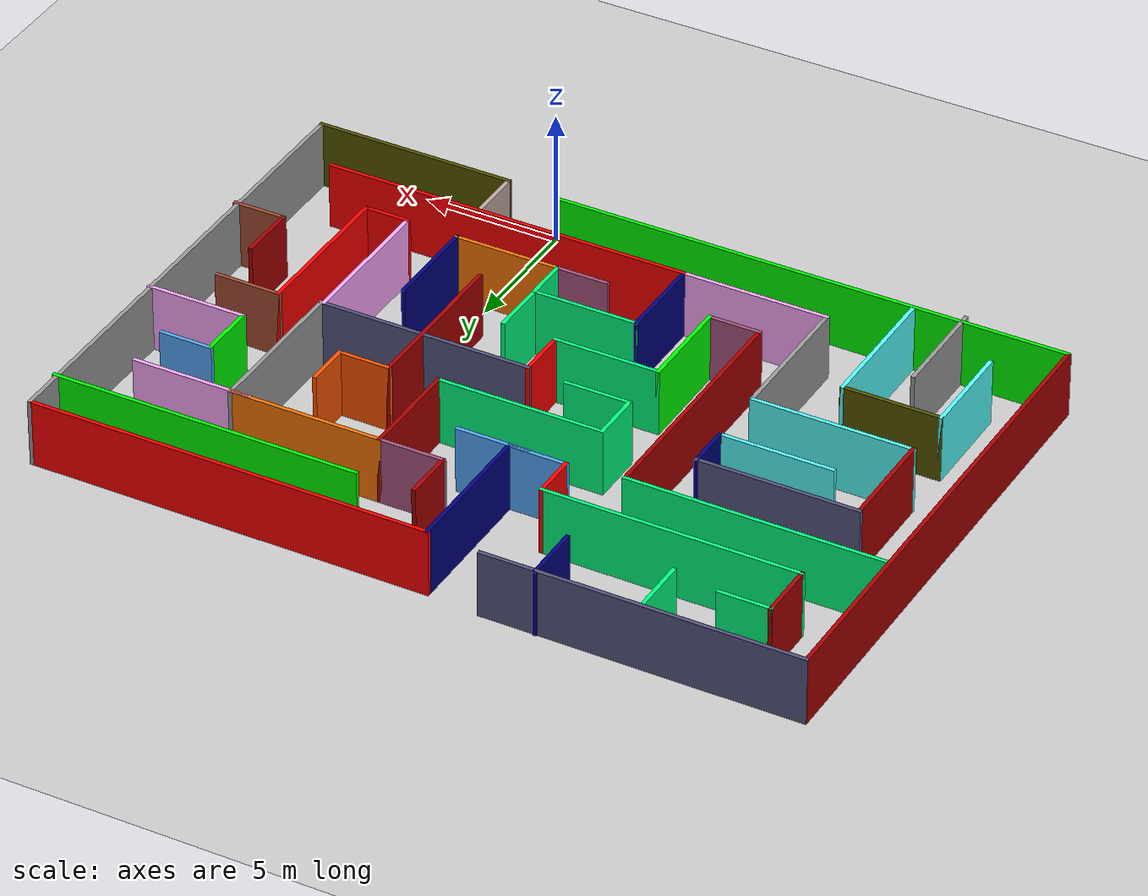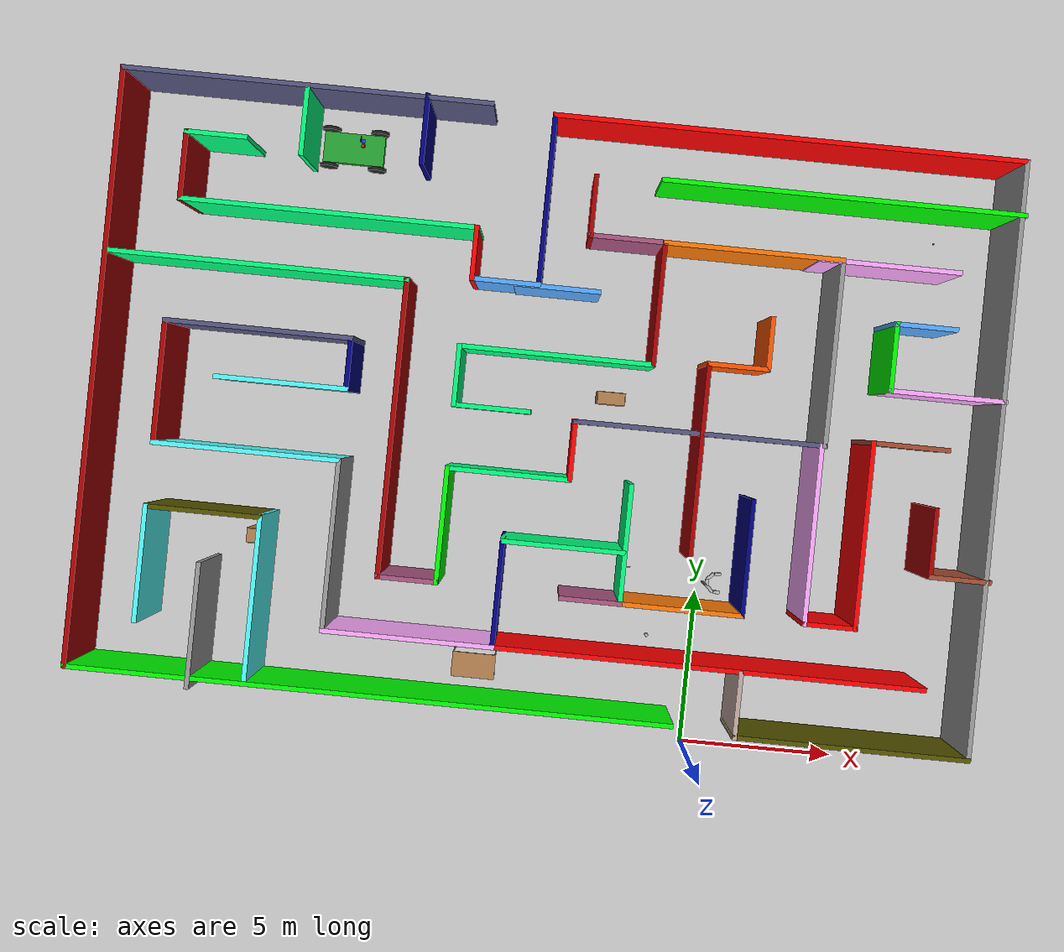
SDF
<sdf version="1.6">
 <world name="default">
  <light name="sun" type="directional">
   <pose>0 0 10 0 -0 0</pose>
   <diffuse>0.8 0.8 0.8 1</diffuse>
   <specular>0.1 0.1 0.1 1</specular>
   <attenuation>
    <range>1000</range>
    <constant>0.9</constant>
    <linear>0.01</linear>
    <quadratic>0.001</quadratic>
   </attenuation>
   <direction>-0.5 0.5 -1</direction>
  </light>
  <model name="ground_plane">
   <static>1</static>
   <link name="link">
    <collision name="collision">
     <geometry><plane><normal>0 0 1</normal><size>100 100</size></plane></geometry>
     <surface><friction><ode><mu>100</mu><mu2>50</mu2></ode></friction></surface>
    </collision>
    <visual name="visual">
     <cast_shadows>0</cast_shadows>
     <geometry><plane><normal>0 0 1</normal><size>100 100</size></plane></geometry>
     <material>
      <script><uri>file://media/materials/scripts/gazebo.material</uri><name>Gazebo/Grey</name></script>
     </material>
    </visual>
   </link>
  </model>
  <gravity>0 0 -9.8</gravity>
  <magnetic_field>6e-06 2.3e-05 -4.2e-05</magnetic_field>
  <atmosphere type="adiabatic"/>
  <physics name="default_physics" default="0" type="ode">
   <max_step_size>0.001</max_step_size>
   <real_time_factor>1</real_time_factor>
   <real_time_update_rate>1000</real_time_update_rate>
  </physics>
  <scene><ambient>0.4 0.4 0.4 1</ambient><background>0.7 0.7 0.7 1</background><shadows>1</shadows></scene>
  <spherical_coordinates>
   <surface_model>EARTH_WGS84</surface_model>
   <latitude_deg>0</latitude_deg>
   <longitude_deg>0</longitude_deg>
   <elevation>0</elevation>
   <heading_deg>0</heading_deg>
  </spherical_coordinates>
  <model name="medium_coloured_maze">
   <pose>-5.4722 10.3379 0 0 -0 0</pose>
   <link name="Wall_0">
    <collision name="Wall_0_Collision">
     <geometry><box><size>19 0.15 2.5</size></box></geometry>
     <pose>0 0 1.25 0 -0 0</pose>
    </collision>
    <visual name="Wall_0_Visual">
     <pose>0 0 1.25 0 -0 0</pose>
     <geometry><box><size>19 0.15 2.5</size></box></geometry>
     <material>
      <script><uri>file://media/materials/scripts/gazebo.material</uri><name>Gazebo/Grey</name></script>
      <ambient>0.666667 0 0 1</ambient>
     </material>
    </visual>
    <pose>-14.2862 0.111227 0 0 0 -1.5708</pose>
   </link>
   <link name="Wall_1">
    <collision name="Wall_1_Collision">
     <geometry><box><size>19.25 0.15 2.5</size></box></geometry>
     <pose>0 0 1.25 0 -0 0</pose>
    </collision>
    <visual name="Wall_1_Visual">
     <pose>0 0 1.25 0 -0 0</pose>
     <geometry><box><size>19.25 0.15 2.5</size></box></geometry>
     <material>
      <script><uri>file://media/materials/scripts/gazebo.material</uri><name>Gazebo/Grey</name></script>
      <ambient>0 1 0 1</ambient>
     </material>
    </visual>
    <pose>-4.73615 -9.31377 0 0 -0 0</pose>
   </link>
   <link name="Wall_10">
    <collision name="Wall_10_Collision">
     <geometry><box><size>2.25 0.15 2.5</size></box></geometry>
     <pose>0 0 1.25 0 -0 0</pose>
    </collision>
    <visual name="Wall_10_Visual">
     <pose>0 0 1.25 0 -0 0</pose>
     <geometry><box><size>2.25 0.15 2.5</size></box></geometry>
     <material>
      <script><uri>file://media/materials/scripts/gazebo.material</uri><name>Gazebo/Grey</name></script>
      <ambient>0.666667 0 0 1</ambient>
     </material>
    </visual>
    <pose>-12.1169 6.6789 0 0 -0 1.5708</pose>
   </link>
   <link name="Wall_11">
    <collision name="Wall_11_Collision">
     <geometry><box><size>2 0.15 2.5</size></box></geometry>
     <pose>0 0 1.25 0 -0 0</pose>
    </collision>
    <visual name="Wall_11_Visual">
     <pose>0 0 1.25 0 -0 0</pose>
     <geometry><box><size>2 0.15 2.5</size></box></geometry>
     <material>
      <script><uri>file://media/materials/scripts/gazebo.material</uri><name>Gazebo/Grey</name></script>
      <ambient>0 1 0.498039 1</ambient>
     </material>
    </visual>
    <pose>-11.1919 7.7289 0 0 -0 0</pose>
   </link>
   <link name="Wall_13">
    <collision name="Wall_13_Collision">
     <geometry><box><size>11.75 0.15 2.5</size></box></geometry>
     <pose>0 0 1.25 0 -0 0</pose>
    </collision>
    <visual name="Wall_13_Visual">
     <pose>0 0 1.25 0 -0 0</pose>
     <geometry><box><size>11.75 0.15 2.5</size></box></geometry>
     <material>
      <script><uri>file://media/materials/scripts/gazebo.material</uri><name>Gazebo/Grey</name></script>
      <ambient>0.333333 0.333333 0.498039 1</ambient>
     </material>
    </visual>
    <pose>-8.48615 9.53623 0 0 -0 0</pose>
   </link>
   <link name="Wall_15">
    <collision name="Wall_15_Collision">
     <geometry><box><size>2.25 0.15 2.5</size></box></geometry>
     <pose>0 0 1.25 0 -0 0</pose>
    </collision>
    <visual name="Wall_15_Visual">
     <pose>0 0 1.25 0 -0 0</pose>
     <geometry><box><size>2.25 0.15 2.5</size></box></geometry>
     <material>
      <script><uri>file://media/materials/scripts/gazebo.material</uri><name>Gazebo/Grey</name></script>
      <ambient>0 1 0.498039 1</ambient>
     </material>
    </visual>
    <pose>-8.47981 8.45384 0 0 0 -1.5708</pose>
   </link>
   <link name="Wall_18">
    <collision name="Wall_18_Collision">
     <geometry><box><size>2.25 0.15 2.5</size></box></geometry>
     <pose>0 0 1.25 0 -0 0</pose>
    </collision>
    <visual name="Wall_18_Visual">
     <pose>0 0 1.25 0 -0 0</pose>
     <geometry><box><size>2.25 0.15 2.5</size></box></geometry>
     <material>
      <script><uri>file://media/materials/scripts/gazebo.material</uri><name>Gazebo/Grey</name></script>
      <ambient>0 0 0.498039 1</ambient>
     </material>
    </visual>
    <pose>-4.69991 8.53531 0 0 0 -1.5708</pose>
   </link>
   <link name="Wall_20">
    <collision name="Wall_20_Collision">
     <geometry><box><size>9.5 0.15 2.5</size></box></geometry>
     <pose>0 0 1.25 0 -0 0</pose>
    </collision>
    <visual name="Wall_20_Visual">
     <pose>0 0 1.25 0 -0 0</pose>
     <geometry><box><size>9.5 0.15 2.5</size></box></geometry>
     <material>
      <script><uri>file://media/materials/scripts/gazebo.material</uri><name>Gazebo/Grey</name></script>
      <ambient>0 1 0.498039 1</ambient>
     </material>
    </visual>
    <pose>-9.46955 3.79078 0 0 -0 0</pose>
   </link>
   <link name="Wall_21">
    <collision name="Wall_21_Collision">
     <geometry><box><size>9.5 0.15 2.5</size></box></geometry>
     <pose>0 0 1.25 0 -0 0</pose>
    </collision>
    <visual name="Wall_21_Visual">
     <pose>0 0 1.25 0 -0 0</pose>
     <geometry><box><size>9.5 0.15 2.5</size></box></geometry>
     <material>
      <script><uri>file://media/materials/scripts/gazebo.material</uri><name>Gazebo/Grey</name></script>
      <ambient>0.666667 0 0 1</ambient>
     </material>
    </visual>
    <pose>-4.79455 -0.884224 0 0 0 -1.5708</pose>
   </link>
   <link name="Wall_22">
    <collision name="Wall_22_Collision">
     <geometry><box><size>2 0.15 2.5</size></box></geometry>
     <pose>0 0 1.25 0 -0 0</pose>
    </collision>
    <visual name="Wall_22_Visual">
     <pose>0 0 1.25 0 -0 0</pose>
     <geometry><box><size>2 0.15 2.5</size></box></geometry>
     <material>
      <script><uri>file://media/materials/scripts/gazebo.material</uri><name>Gazebo/Grey</name></script>
      <ambient>0.666667 0.333333 0.498039 1</ambient>
     </material>
    </visual>
    <pose>-3.86955 -5.55922 0 0 -0 0</pose>
   </link>
   <link name="Wall_23">
    <collision name="Wall_23_Collision">
     <geometry><box><size>3.75 0.15 2.5</size></box></geometry>
     <pose>0 0 1.25 0 -0 0</pose>
    </collision>
    <visual name="Wall_23_Visual">
     <pose>0 0 1.25 0 -0 0</pose>
     <geometry><box><size>3.75 0.15 2.5</size></box></geometry>
     <material>
      <script><uri>file://media/materials/scripts/gazebo.material</uri><name>Gazebo/Grey</name></script>
      <ambient>0 1 0 1</ambient>
     </material>
    </visual>
    <pose>-2.94455 -3.75922 0 0 -0 1.5708</pose>
   </link>
   <link name="Wall_24">
    <collision name="Wall_24_Collision">
     <geometry><box><size>4 0.15 2.5</size></box></geometry>
     <pose>0 0 1.25 0 -0 0</pose>
    </collision>
    <visual name="Wall_24_Visual">
     <pose>0 0 1.25 0 -0 0</pose>
     <geometry><box><size>4 0.15 2.5</size></box></geometry>
     <material>
      <script><uri>file://media/materials/scripts/gazebo.material</uri><name>Gazebo/Grey</name></script>
      <ambient>0 1 0.498039 1</ambient>
     </material>
    </visual>
    <pose>-1.01955 -1.95922 0 0 -0 0</pose>
   </link>
   <link name="Wall_25">
    <collision name="Wall_25_Collision">
     <geometry><box><size>2 0.15 2.5</size></box></geometry>
     <pose>0 0 1.25 0 -0 0</pose>
    </collision>
    <visual name="Wall_25_Visual">
     <pose>0 0 1.25 0 -0 0</pose>
     <geometry><box><size>2 0.15 2.5</size></box></geometry>
     <material>
      <script><uri>file://media/materials/scripts/gazebo.material</uri><name>Gazebo/Grey</name></script>
      <ambient>1 0 0 1</ambient>
     </material>
    </visual>
    <pose>0.905454 -1.03422 0 0 -0 1.5708</pose>
   </link>
   <link name="Wall_26">
    <collision name="Wall_26_Collision">
     <geometry><box><size>8 0.15 2.5</size></box></geometry>
     <pose>0 0 1.25 0 -0 0</pose>
    </collision>
    <visual name="Wall_26_Visual">
     <pose>0 0 1.25 0 -0 0</pose>
     <geometry><box><size>8 0.15 2.5</size></box></geometry>
     <material>
      <script><uri>file://media/materials/scripts/gazebo.material</uri><name>Gazebo/Grey</name></script>
      <ambient>0.333333 0.333333 0.498039 1</ambient>
     </material>
    </visual>
    <pose>4.83045 -0.109224 0 0 -0 0</pose>
   </link>
   <link name="Wall_27">
    <collision name="Wall_27_Collision">
     <geometry><box><size>6 0.15 2.5</size></box></geometry>
     <pose>0 0 1.25 0 -0 0</pose>
    </collision>
    <visual name="Wall_27_Visual">
     <pose>0 0 1.25 0 -0 0</pose>
     <geometry><box><size>6 0.15 2.5</size></box></geometry>
     <material>
      <script><uri>file://media/materials/scripts/gazebo.material</uri><name>Gazebo/Grey</name></script>
      <ambient>0 0 0 1</ambient>
     </material>
    </visual>
    <pose>8.75545 2.81578 0 0 -0 1.5708</pose>
   </link>
   <link name="Wall_28">
    <collision name="Wall_28_Collision">
     <geometry><box><size>5.75 0.15 2.5</size></box></geometry>
     <pose>0 0 1.25 0 -0 0</pose>
    </collision>
    <visual name="Wall_28_Visual">
     <pose>0 0 1.25 0 -0 0</pose>
     <geometry><box><size>5.75 0.15 2.5</size></box></geometry>
     <material>
      <script><uri>file://media/materials/scripts/gazebo.material</uri><name>Gazebo/Grey</name></script>
      <ambient>0.996078 0.47451 0.0196078 1</ambient>
     </material>
    </visual>
    <pose>5.95545 5.74078 0 0 -0 3.14159</pose>
   </link>
   <link name="Wall_29">
    <collision name="Wall_29_Collision">
     <geometry><box><size>4 0.15 2.5</size></box></geometry>
     <pose>0 0 1.25 0 -0 0</pose>
    </collision>
    <visual name="Wall_29_Visual">
     <pose>0 0 1.25 0 -0 0</pose>
     <geometry><box><size>4 0.15 2.5</size></box></geometry>
     <material>
      <script><uri>file://media/materials/scripts/gazebo.material</uri><name>Gazebo/Grey</name></script>
      <ambient>0.666667 0 0 1</ambient>
     </material>
    </visual>
    <pose>3.15545 3.81578 0 0 0 -1.5708</pose>
   </link>
   <link name="Wall_3">
    <collision name="Wall_3_Collision">
     <geometry><box><size>7.5 0.15 2.5</size></box></geometry>
     <pose>0 0 1.25 0 -0 0</pose>
    </collision>
    <visual name="Wall_3_Visual">
     <pose>0 0 1.25 0 -0 0</pose>
     <geometry><box><size>7.5 0.15 2.5</size></box></geometry>
     <material>
      <script><uri>file://media/materials/scripts/gazebo.material</uri><name>Gazebo/Grey</name></script>
      <ambient>0.333333 0.333333 0 1</ambient>
     </material>
    </visual>
    <pose>10.5081 -9.4711 0 0 -0 0</pose>
   </link>
   <link name="Wall_30">
    <collision name="Wall_30_Collision">
     <geometry><box><size>6.25 0.15 2.5</size></box></geometry>
     <pose>0 0 1.25 0 -0 0</pose>
    </collision>
    <visual name="Wall_30_Visual">
     <pose>0 0 1.25 0 -0 0</pose>
     <geometry><box><size>6.25 0.15 2.5</size></box></geometry>
     <material>
      <script><uri>file://media/materials/scripts/gazebo.material</uri><name>Gazebo/Grey</name></script>
      <ambient>0 1 0.498039 1</ambient>
     </material>
    </visual>
    <pose>0.105454 1.89078 0 0 -0 3.14159</pose>
   </link>
   <link name="Wall_31">
    <collision name="Wall_31_Collision">
     <geometry><box><size>2 0.15 2.5</size></box></geometry>
     <pose>0 0 1.25 0 -0 0</pose>
    </collision>
    <visual name="Wall_31_Visual">
     <pose>0 0 1.25 0 -0 0</pose>
     <geometry><box><size>2 0.15 2.5</size></box></geometry>
     <material>
      <script><uri>file://media/materials/scripts/gazebo.material</uri><name>Gazebo/Grey</name></script>
      <ambient>0 1 0.498039 1</ambient>
     </material>
    </visual>
    <pose>-2.94455 0.965776 0 0 0 -1.5708</pose>
   </link>
   <link name="Wall_32">
    <collision name="Wall_32_Collision">
     <geometry><box><size>2.5 0.15 2.5</size></box></geometry>
     <pose>0 0 1.25 0 -0 0</pose>
    </collision>
    <visual name="Wall_32_Visual">
     <pose>0 0 1.25 0 -0 0</pose>
     <geometry><box><size>2.5 0.15 2.5</size></box></geometry>
     <material>
      <script><uri>file://media/materials/scripts/gazebo.material</uri><name>Gazebo/Grey</name></script>
      <ambient>0 1 0.498039 1</ambient>
     </material>
    </visual>
    <pose>-1.76955 0.040776 0 0 -0 0</pose>
   </link>
   <link name="Wall_34">
    <collision name="Wall_34_Collision">
     <geometry><box><size>4.25 0.15 2.5</size></box></geometry>
     <pose>0 0 1.25 0 -0 0</pose>
    </collision>
    <visual name="Wall_34_Visual">
     <pose>0 0 1.25 0 -0 0</pose>
     <geometry><box><size>4.25 0.15 2.5</size></box></geometry>
     <material>
      <script><uri>file://media/materials/scripts/gazebo.material</uri><name>Gazebo/Grey</name></script>
      <ambient>0.333333 1 1 1</ambient>
     </material>
    </visual>
    <pose>-8.39882 0.186302 0 0 -0 0</pose>
   </link>
   <link name="Wall_35">
    <collision name="Wall_35_Collision">
     <geometry><box><size>1.75 0.15 2.5</size></box></geometry>
     <pose>0 0 1.25 0 -0 0</pose>
    </collision>
    <visual name="Wall_35_Visual">
     <pose>0 0 1.25 0 -0 0</pose>
     <geometry><box><size>1.75 0.15 2.5</size></box></geometry>
     <material>
      <script><uri>file://media/materials/scripts/gazebo.material</uri><name>Gazebo/Grey</name></script>
      <ambient>0 0 0.498039 1</ambient>
     </material>
    </visual>
    <pose>-6.34882 0.986302 0 0 -0 1.5708</pose>
   </link>
   <link name="Wall_36">
    <collision name="Wall_36_Collision">
     <geometry><box><size>6 0.15 2.5</size></box></geometry>
     <pose>0 0 1.25 0 -0 0</pose>
    </collision>
    <visual name="Wall_36_Visual">
     <pose>0 0 1.25 0 -0 0</pose>
     <geometry><box><size>6 0.15 2.5</size></box></geometry>
     <material>
      <script><uri>file://media/materials/scripts/gazebo.material</uri><name>Gazebo/Grey</name></script>
      <ambient>0.333333 0.333333 0.498039 1</ambient>
     </material>
    </visual>
    <pose>-9.27382 1.7863 0 0 -0 3.14159</pose>
   </link>
   <link name="Wall_37">
    <collision name="Wall_37_Collision">
     <geometry><box><size>4 0.15 2.5</size></box></geometry>
     <pose>0 0 1.25 0 -0 0</pose>
    </collision>
    <visual name="Wall_37_Visual">
     <pose>0 0 1.25 0 -0 0</pose>
     <geometry><box><size>4 0.15 2.5</size></box></geometry>
     <material>
      <script><uri>file://media/materials/scripts/gazebo.material</uri><name>Gazebo/Grey</name></script>
      <ambient>0.666667 0 0 1</ambient>
     </material>
    </visual>
    <pose>-12.1988 -0.138698 0 0 0 -1.5708</pose>
   </link>
   <link name="Wall_38">
    <collision name="Wall_38_Collision">
     <geometry><box><size>6 0.15 2.5</size></box></geometry>
     <pose>0 0 1.25 0 -0 0</pose>
    </collision>
    <visual name="Wall_38_Visual">
     <pose>0 0 1.25 0 -0 0</pose>
     <geometry><box><size>6 0.15 2.5</size></box></geometry>
     <material>
      <script><uri>file://media/materials/scripts/gazebo.material</uri><name>Gazebo/Grey</name></script>
      <ambient>0.333333 1 1 1</ambient>
     </material>
    </visual>
    <pose>-9.27382 -2.0637 0 0 -0 0</pose>
   </link>
   <link name="Wall_39">
    <collision name="Wall_39_Collision">
     <geometry><box><size>5.5 0.15 2.5</size></box></geometry>
     <pose>0 0 1.25 0 -0 0</pose>
    </collision>
    <visual name="Wall_39_Visual">
     <pose>0 0 1.25 0 -0 0</pose>
     <geometry><box><size>5.5 0.15 2.5</size></box></geometry>
     <material>
      <script><uri>file://media/materials/scripts/gazebo.material</uri><name>Gazebo/Grey</name></script>
      <ambient>0 0 0 1</ambient>
     </material>
    </visual>
    <pose>-6.34882 -4.7387 0 0 0 -1.5708</pose>
   </link>
   <link name="Wall_4">
    <collision name="Wall_4_Collision">
     <geometry><box><size>19 0.15 2.5</size></box></geometry>
     <pose>0 0 1.25 0 -0 0</pose>
    </collision>
    <visual name="Wall_4_Visual">
     <pose>0 0 1.25 0 -0 0</pose>
     <geometry><box><size>19 0.15 2.5</size></box></geometry>
     <material>
      <script><uri>file://media/materials/scripts/gazebo.material</uri><name>Gazebo/Grey</name></script>
      <ambient>0 0 0 1</ambient>
     </material>
    </visual>
    <pose>14.1831 -0.046098 0 0 -0 1.5708</pose>
   </link>
   <link name="Wall_40">
    <collision name="Wall_40_Collision">
     <geometry><box><size>5.5 0.15 2.5</size></box></geometry>
     <pose>0 0 1.25 0 -0 0</pose>
    </collision>
    <visual name="Wall_40_Visual">
     <pose>0 0 1.25 0 -0 0</pose>
     <geometry><box><size>5.5 0.15 2.5</size></box></geometry>
     <material>
      <script><uri>file://media/materials/scripts/gazebo.material</uri><name>Gazebo/Grey</name></script>
      <ambient>1 0.666667 1 1</ambient>
     </material>
    </visual>
    <pose>-3.67382 -7.4137 0 0 -0 0</pose>
   </link>
   <link name="Wall_41">
    <collision name="Wall_41_Collision">
     <geometry><box><size>3.5 0.15 2.5</size></box></geometry>
     <pose>0 0 1.25 0 -0 0</pose>
    </collision>
    <visual name="Wall_41_Visual">
     <pose>0 0 1.25 0 -0 0</pose>
     <geometry><box><size>3.5 0.15 2.5</size></box></geometry>
     <material>
      <script><uri>file://media/materials/scripts/gazebo.material</uri><name>Gazebo/Grey</name></script>
      <ambient>0 0 0.498039 1</ambient>
     </material>
    </visual>
    <pose>-0.99882 -5.7387 0 0 -0 1.5708</pose>
   </link>
   <link name="Wall_42">
    <collision name="Wall_42_Collision">
     <geometry><box><size>4 0.15 2.5</size></box></geometry>
     <pose>0 0 1.25 0 -0 0</pose>
    </collision>
    <visual name="Wall_42_Visual">
     <pose>0 0 1.25 0 -0 0</pose>
     <geometry><box><size>4 0.15 2.5</size></box></geometry>
     <material>
      <script><uri>file://media/materials/scripts/gazebo.material</uri><name>Gazebo/Grey</name></script>
      <ambient>0 1 0.498039 1</ambient>
     </material>
    </visual>
    <pose>0.92618 -4.0637 0 0 -0 0</pose>
   </link>
   <link name="Wall_43">
    <collision name="Wall_43_Collision">
     <geometry><box><size>1.75 0.15 2.5</size></box></geometry>
     <pose>0 0 1.25 0 -0 0</pose>
    </collision>
    <visual name="Wall_43_Visual">
     <pose>0 0 1.25 0 -0 0</pose>
     <geometry><box><size>1.75 0.15 2.5</size></box></geometry>
     <material>
      <script><uri>file://media/materials/scripts/gazebo.material</uri><name>Gazebo/Grey</name></script>
      <ambient>0 1 0.498039 1</ambient>
     </material>
    </visual>
    <pose>2.85118 -4.8637 0 0 0 -1.5708</pose>
   </link>
   <link name="Wall_44">
    <collision name="Wall_44_Collision">
     <geometry><box><size>4 0.15 2.5</size></box></geometry>
     <pose>0 0 1.25 0 -0 0</pose>
    </collision>
    <visual name="Wall_44_Visual">
     <pose>0 0 1.25 0 -0 0</pose>
     <geometry><box><size>4 0.15 2.5</size></box></geometry>
     <material>
      <script><uri>file://media/materials/scripts/gazebo.material</uri><name>Gazebo/Grey</name></script>
      <ambient>0.996078 0.47451 0.0196078 1</ambient>
     </material>
    </visual>
    <pose>4.77618 -5.6637 0 0 -0 0</pose>
   </link>
   <link name="Wall_45">
    <collision name="Wall_45_Collision">
     <geometry><box><size>3.75 0.15 2.5</size></box></geometry>
     <pose>0 0 1.25 0 -0 0</pose>
    </collision>
    <visual name="Wall_45_Visual">
     <pose>0 0 1.25 0 -0 0</pose>
     <geometry><box><size>3.75 0.15 2.5</size></box></geometry>
     <material>
      <script><uri>file://media/materials/scripts/gazebo.material</uri><name>Gazebo/Grey</name></script>
      <ambient>0 0 0.498039 1</ambient>
     </material>
    </visual>
    <pose>6.70118 -3.8637 0 0 -0 1.5708</pose>
   </link>
   <link name="Wall_47">
    <collision name="Wall_47_Collision">
     <geometry><box><size>1.75 0.15 2.5</size></box></geometry>
     <pose>0 0 1.25 0 -0 0</pose>
    </collision>
    <visual name="Wall_47_Visual">
     <pose>0 0 1.25 0 -0 0</pose>
     <geometry><box><size>1.75 0.15 2.5</size></box></geometry>
     <material>
      <script><uri>file://media/materials/scripts/gazebo.material</uri><name>Gazebo/Grey</name></script>
      <ambient>1 0.333333 0 1</ambient>
     </material>
    </visual>
    <pose>6.75228 2.89952 0 0 0 -1.5708</pose>
   </link>
   <link name="Wall_48">
    <collision name="Wall_48_Collision">
     <geometry><box><size>2 0.15 2.5</size></box></geometry>
     <pose>0 0 1.25 0 -0 0</pose>
    </collision>
    <visual name="Wall_48_Visual">
     <pose>0 0 1.25 0 -0 0</pose>
     <geometry><box><size>2 0.15 2.5</size></box></geometry>
     <material>
      <script><uri>file://media/materials/scripts/gazebo.material</uri><name>Gazebo/Grey</name></script>
      <ambient>1 0.333333 0 1</ambient>
     </material>
    </visual>
    <pose>5.82728 2.09952 0 0 -0 3.14159</pose>
   </link>
   <link name="Wall_49">
    <collision name="Wall_49_Collision">
     <geometry><box><size>6.25 0.15 2.5</size></box></geometry>
     <pose>0 0 1.25 0 -0 0</pose>
    </collision>
    <visual name="Wall_49_Visual">
     <pose>0 0 1.25 0 -0 0</pose>
     <geometry><box><size>6.25 0.15 2.5</size></box></geometry>
     <material>
      <script><uri>file://media/materials/scripts/gazebo.material</uri><name>Gazebo/Grey</name></script>
      <ambient>0.666667 0 0 1</ambient>
     </material>
    </visual>
    <pose>4.90228 -0.950477 0 0 0 -1.5708</pose>
   </link>
   <link name="Wall_5">
    <collision name="Wall_5_Collision">
     <geometry><box><size>15 0.15 2.5</size></box></geometry>
     <pose>0 0 1.25 0 -0 0</pose>
    </collision>
    <visual name="Wall_5_Visual">
     <pose>0 0 1.25 0 -0 0</pose>
     <geometry><box><size>15 0.15 2.5</size></box></geometry>
     <material>
      <script><uri>file://media/materials/scripts/gazebo.material</uri><name>Gazebo/Grey</name></script>
      <ambient>1 0 0 1</ambient>
     </material>
    </visual>
    <pose>6.7581 9.3789 0 0 -0 3.14159</pose>
   </link>
   <link name="Wall_51">
    <collision name="Wall_51_Collision">
     <geometry><box><size>2.25 0.15 2.5</size></box></geometry>
     <pose>0 0 1.25 0 -0 0</pose>
    </collision>
    <visual name="Wall_51_Visual">
     <pose>0 0 1.25 0 -0 0</pose>
     <geometry><box><size>2.25 0.15 2.5</size></box></geometry>
     <material>
      <script><uri>file://media/materials/scripts/gazebo.material</uri><name>Gazebo/Grey</name></script>
      <ambient>0 1 0.498039 1</ambient>
     </material>
    </visual>
    <pose>2.85118 -3.0137 0 0 -0 1.5708</pose>
   </link>
   <link name="Wall_53">
    <collision name="Wall_53_Collision">
     <geometry><box><size>2 0.15 2.5</size></box></geometry>
     <pose>0 0 1.25 0 -0 0</pose>
    </collision>
    <visual name="Wall_53_Visual">
     <pose>0 0 1.25 0 -0 0</pose>
     <geometry><box><size>2 0.15 2.5</size></box></geometry>
     <material>
      <script><uri>file://media/materials/scripts/gazebo.material</uri><name>Gazebo/Grey</name></script>
      <ambient>0.666667 0.333333 0.498039 1</ambient>
     </material>
    </visual>
    <pose>1.92618 -5.6637 0 0 -0 3.14159</pose>
   </link>
   <link name="Wall_56">
    <collision name="Wall_56_Collision">
     <geometry><box><size>13.75 0.15 2.5</size></box></geometry>
     <pose>0 0 1.25 0 -0 0</pose>
    </collision>
    <visual name="Wall_56_Visual">
     <pose>0 0 1.25 0 -0 0</pose>
     <geometry><box><size>13.75 0.15 2.5</size></box></geometry>
     <material>
      <script><uri>file://media/materials/scripts/gazebo.material</uri><name>Gazebo/Grey</name></script>
      <ambient>1 0 0 1</ambient>
     </material>
    </visual>
    <pose>5.80118 -7.4137 0 0 -0 0</pose>
   </link>
   <link name="Wall_58">
    <collision name="Wall_58_Collision">
     <geometry><box><size>2.16629 0.15 2.5</size></box></geometry>
     <pose>0 0 1.25 0 -0 0</pose>
    </collision>
    <visual name="Wall_58_Visual">
     <pose>0 0 1.25 0 -0 0</pose>
     <geometry><box><size>2.16629 0.15 2.5</size></box></geometry>
     <material>
      <script><uri>file://media/materials/scripts/gazebo.material</uri><name>Gazebo/Grey</name></script>
      <ambient>0.760784 0.662745 0.627451 1</ambient>
     </material>
    </visual>
    <pose>6.84013 -8.46298 0 0 0 -1.57777</pose>
   </link>
   <link name="Wall_6">
    <collision name="Wall_6_Collision">
     <geometry><box><size>5.5 0.15 2.5</size></box></geometry>
     <pose>0 0 1.25 0 -0 0</pose>
    </collision>
    <visual name="Wall_6_Visual">
     <pose>0 0 1.25 0 -0 0</pose>
     <geometry><box><size>5.5 0.15 2.5</size></box></geometry>
     <material>
      <script><uri>file://media/materials/scripts/gazebo.material</uri><name>Gazebo/Grey</name></script>
      <ambient>0 0 0.498039 1</ambient>
     </material>
    </visual>
    <pose>-0.666901 6.7039 0 0 0 -1.5708</pose>
   </link>
   <link name="Wall_60">
    <collision name="Wall_60_Collision">
     <geometry><box><size>2.5 0.15 2.5</size></box></geometry>
     <pose>0 0 1.25 0 -0 0</pose>
    </collision>
    <visual name="Wall_60_Visual">
     <pose>0 0 1.25 0 -0 0</pose>
     <geometry><box><size>2.5 0.15 2.5</size></box></geometry>
     <material>
      <script><uri>file://media/materials/scripts/gazebo.material</uri><name>Gazebo/Bricks</name></script>
      <ambient>1 1 1 1</ambient>
     </material>
    </visual>
    <pose>11.4337 0.135142 0 0 -0 3.14159</pose>
   </link>
   <link name="Wall_61">
    <collision name="Wall_61_Collision">
     <geometry><box><size>6 0.15 2.5</size></box></geometry>
     <pose>0 0 1.25 0 -0 0</pose>
    </collision>
    <visual name="Wall_61_Visual">
     <pose>0 0 1.25 0 -0 0</pose>
     <geometry><box><size>6 0.15 2.5</size></box></geometry>
     <material>
      <script><uri>file://media/materials/scripts/gazebo.material</uri><name>Gazebo/Grey</name></script>
      <ambient>1 0 0 1</ambient>
     </material>
    </visual>
    <pose>10.2587 -2.78986 0 0 0 -1.5708</pose>
   </link>
   <link name="Wall_62">
    <collision name="Wall_62_Collision">
     <geometry><box><size>1.75 0.15 2.5</size></box></geometry>
     <pose>0 0 1.25 0 -0 0</pose>
    </collision>
    <visual name="Wall_62_Visual">
     <pose>0 0 1.25 0 -0 0</pose>
     <geometry><box><size>1.75 0.15 2.5</size></box></geometry>
     <material>
      <script><uri>file://media/materials/scripts/gazebo.material</uri><name>Gazebo/Grey</name></script>
      <ambient>1 0 0 1</ambient>
     </material>
    </visual>
    <pose>9.45865 -5.71486 0 0 -0 3.14159</pose>
   </link>
   <link name="Wall_63">
    <collision name="Wall_63_Collision">
     <geometry><box><size>5.75 0.15 2.5</size></box></geometry>
     <pose>0 0 1.25 0 -0 0</pose>
    </collision>
    <visual name="Wall_63_Visual">
     <pose>0 0 1.25 0 -0 0</pose>
     <geometry><box><size>5.75 0.15 2.5</size></box></geometry>
     <material>
      <script><uri>file://media/materials/scripts/gazebo.material</uri><name>Gazebo/Grey</name></script>
      <ambient>1 0.666667 1 1</ambient>
     </material>
    </visual>
    <pose>8.65865 -2.91486 0 0 -0 1.5708</pose>
   </link>
   <link name="Wall_65">
    <collision name="Wall_65_Collision">
     <geometry><box><size>2.25 0.15 2.5</size></box></geometry>
     <pose>0 0 1.25 0 -0 0</pose>
    </collision>
    <visual name="Wall_65_Visual">
     <pose>0 0 1.25 0 -0 0</pose>
     <geometry><box><size>2.25 0.15 2.5</size></box></geometry>
     <material>
      <script><uri>file://media/materials/scripts/gazebo.material</uri><name>Gazebo/Grey</name></script>
      <ambient>0.666667 0 0 1</ambient>
     </material>
    </visual>
    <pose>12.4362 -2.81236 0 0 0 -1.5708</pose>
   </link>
   <link name="Wall_66">
    <collision name="Wall_66_Collision">
     <geometry><box><size>2 0.15 2.5</size></box></geometry>
     <pose>0 0 1.25 0 -0 0</pose>
    </collision>
    <visual name="Wall_66_Visual">
     <pose>0 0 1.25 0 -0 0</pose>
     <geometry><box><size>2 0.15 2.5</size></box></geometry>
     <material>
      <script><uri>file://media/materials/scripts/gazebo.material</uri><name>Gazebo/Bricks</name></script>
      <ambient>1 1 1 1</ambient>
     </material>
    </visual>
    <pose>13.3612 -3.86236 0 0 -0 0</pose>
   </link>
   <link name="Wall_68">
    <collision name="Wall_68_Collision">
     <geometry><box><size>11.5 0.15 2.5</size></box></geometry>
     <pose>0 0 1.25 0 -0 0</pose>
    </collision>
    <visual name="Wall_68_Visual">
     <pose>0 0 1.25 0 -0 0</pose>
     <geometry><box><size>11.5 0.15 2.5</size></box></geometry>
     <material>
      <script><uri>file://media/materials/scripts/gazebo.material</uri><name>Gazebo/Grey</name></script>
      <ambient>0 1 0 1</ambient>
     </material>
    </visual>
    <pose>8.60983 7.69706 0 0 -0 0</pose>
   </link>
   <link name="Wall_7">
    <collision name="Wall_7_Collision">
     <geometry><box><size>2.25 0.15 2.5</size></box></geometry>
     <pose>0 0 1.25 0 -0 0</pose>
    </collision>
    <visual name="Wall_7_Visual">
     <pose>0 0 1.25 0 -0 0</pose>
     <geometry><box><size>2.25 0.15 2.5</size></box></geometry>
     <material>
      <script><uri>file://media/materials/scripts/gazebo.material</uri><name>Gazebo/Grey</name></script>
      <ambient>0.333333 0.666667 1 1</ambient>
     </material>
    </visual>
    <pose>-1.7169 4.0289 0 0 -0 3.14159</pose>
   </link>
   <link name="Wall_70">
    <collision name="Wall_70_Collision">
     <geometry><box><size>2 0.15 2.5</size></box></geometry>
     <pose>0 0 1.25 0 -0 0</pose>
    </collision>
    <visual name="Wall_70_Visual">
     <pose>0 0 1.25 0 -0 0</pose>
     <geometry><box><size>2 0.15 2.5</size></box></geometry>
     <material>
      <script><uri>file://media/materials/scripts/gazebo.material</uri><name>Gazebo/Grey</name></script>
      <ambient>0.333333 0.666667 1 1</ambient>
     </material>
    </visual>
    <pose>11.5594 3.91921 0 0 -0 3.14159</pose>
   </link>
   <link name="Wall_71">
    <collision name="Wall_71_Collision">
     <geometry><box><size>2.25 0.15 2.5</size></box></geometry>
     <pose>0 0 1.25 0 -0 0</pose>
    </collision>
    <visual name="Wall_71_Visual">
     <pose>0 0 1.25 0 -0 0</pose>
     <geometry><box><size>2.25 0.15 2.5</size></box></geometry>
     <material>
      <script><uri>file://media/materials/scripts/gazebo.material</uri><name>Gazebo/Grey</name></script>
      <ambient>0 1 0 1</ambient>
     </material>
    </visual>
    <pose>10.6344 2.86921 0 0 0 -1.5708</pose>
   </link>
   <link name="Wall_72">
    <collision name="Wall_72_Collision">
     <geometry><box><size>3.75 0.15 2.5</size></box></geometry>
     <pose>0 0 1.25 0 -0 0</pose>
    </collision>
    <visual name="Wall_72_Visual">
     <pose>0 0 1.25 0 -0 0</pose>
     <geometry><box><size>3.75 0.15 2.5</size></box></geometry>
     <material>
      <script><uri>file://media/materials/scripts/gazebo.material</uri><name>Gazebo/Grey</name></script>
      <ambient>1 0.666667 1 1</ambient>
     </material>
    </visual>
    <pose>12.4344 1.81921 0 0 -0 0</pose>
   </link>
   <link name="Wall_74">
    <collision name="Wall_74_Collision">
     <geometry><box><size>3.75 0.15 2.5</size></box></geometry>
     <pose>0 0 1.25 0 -0 0</pose>
    </collision>
    <visual name="Wall_74_Visual">
     <pose>0 0 1.25 0 -0 0</pose>
     <geometry><box><size>3.75 0.15 2.5</size></box></geometry>
     <material>
      <script><uri>file://media/materials/scripts/gazebo.material</uri><name>Gazebo/Grey</name></script>
      <ambient>0.333333 1 1 1</ambient>
     </material>
    </visual>
    <pose>-12.2291 -5.87671 0 0 -0 1.5708</pose>
   </link>
   <link name="Wall_75">
    <collision name="Wall_75_Collision">
     <geometry><box><size>3.75 0.15 2.5</size></box></geometry>
     <pose>0 0 1.25 0 -0 0</pose>
    </collision>
    <visual name="Wall_75_Visual">
     <pose>0 0 1.25 0 -0 0</pose>
     <geometry><box><size>3.75 0.15 2.5</size></box></geometry>
     <material>
      <script><uri>file://media/materials/scripts/gazebo.material</uri><name>Gazebo/Grey</name></script>
      <ambient>0.333333 0.333333 0 1</ambient>
     </material>
    </visual>
    <pose>-10.4291 -4.07671 0 0 -0 0</pose>
   </link>
   <link name="Wall_76">
    <collision name="Wall_76_Collision">
     <geometry><box><size>5.25 0.15 2.5</size></box></geometry>
     <pose>0 0 1.25 0 -0 0</pose>
    </collision>
    <visual name="Wall_76_Visual">
     <pose>0 0 1.25 0 -0 0</pose>
     <geometry><box><size>5.25 0.15 2.5</size></box></geometry>
     <material>
      <script><uri>file://media/materials/scripts/gazebo.material</uri><name>Gazebo/Grey</name></script>
      <ambient>0.333333 1 1 1</ambient>
     </material>
    </visual>
    <pose>-8.62905 -6.62671 0 0 0 -1.5708</pose>
   </link>
   <link name="Wall_78">
    <collision name="Wall_78_Collision">
     <geometry><box><size>4 0.15 2.5</size></box></geometry>
     <pose>0 0 1.25 0 -0 0</pose>
    </collision>
    <visual name="Wall_78_Visual">
     <pose>0 0 1.25 0 -0 0</pose>
     <geometry><box><size>4 0.15 2.5</size></box></geometry>
     <material>
      <script><uri>file://media/materials/scripts/gazebo.material</uri><name>Gazebo/Grey</name></script>
      <ambient>0 0 0 1</ambient>
     </material>
    </visual>
    <pose>-10.3926 -7.66031 0 0 0 -1.5708</pose>
   </link>
   <link name="Wall_8">
    <collision name="Wall_8_Collision">
     <geometry><box><size>1.75 0.15 2.5</size></box></geometry>
     <pose>0 0 1.25 0 -0 0</pose>
    </collision>
    <visual name="Wall_8_Visual">
     <pose>0 0 1.25 0 -0 0</pose>
     <geometry><box><size>1.75 0.15 2.5</size></box></geometry>
     <material>
      <script><uri>file://media/materials/scripts/gazebo.material</uri><name>Gazebo/Grey</name></script>
      <ambient>1 0 0 1</ambient>
     </material>
    </visual>
    <pose>-2.7669 4.8289 0 0 -0 1.5708</pose>
   </link>
   <link name="Wall_80">
    <collision name="Wall_80_Collision">
     <geometry><box><size>4.5 0.15 2.5</size></box></geometry>
     <pose>0 0 1.25 0 -0 0</pose>
    </collision>
    <visual name="Wall_80_Visual">
     <pose>0 0 1.25 0 -0 0</pose>
     <geometry><box><size>4.5 0.15 2.5</size></box></geometry>
     <material>
      <script><uri>file://media/materials/scripts/gazebo.material</uri><name>Gazebo/Grey</name></script>
      <ambient>1 0.666667 1 1</ambient>
     </material>
    </visual>
    <pose>10.2519 5.70319 0 0 -0 0</pose>
   </link>
   <link name="Wall_84">
    <collision name="Wall_84_Collision">
     <geometry><box><size>2.75 0.15 2.5</size></box></geometry>
     <pose>0 0 1.25 0 -0 0</pose>
    </collision>
    <visual name="Wall_84_Visual">
     <pose>0 0 1.25 0 -0 0</pose>
     <geometry><box><size>2.75 0.15 2.5</size></box></geometry>
     <material>
      <script><uri>file://media/materials/scripts/gazebo.material</uri><name>Gazebo/Grey</name></script>
      <ambient>0.333333 0.666667 1 1</ambient>
     </material>
    </visual>
    <pose>-0.070687 3.99264 0 0 -0 0</pose>
   </link>
   <link name="Wall_86">
    <collision name="Wall_86_Collision">
     <geometry><box><size>2.5 0.15 2.5</size></box></geometry>
     <pose>0 0 1.25 0 -0 0</pose>
    </collision>
    <visual name="Wall_86_Visual">
     <pose>0 0 1.25 0 -0 0</pose>
     <geometry><box><size>2.5 0.15 2.5</size></box></geometry>
     <material>
      <script><uri>file://media/materials/scripts/gazebo.material</uri><name>Gazebo/Grey</name></script>
      <ambient>0.666667 0.333333 0.498039 1</ambient>
     </material>
    </visual>
    <pose>1.98045 5.74078 0 0 -0 3.14159</pose>
   </link>
   <link name="Wall_87">
    <collision name="Wall_87_Collision">
     <geometry><box><size>2 0.15 2.5</size></box></geometry>
     <pose>0 0 1.25 0 -0 0</pose>
    </collision>
    <visual name="Wall_87_Visual">
     <pose>0 0 1.25 0 -0 0</pose>
     <geometry><box><size>2 0.15 2.5</size></box></geometry>
     <material>
      <script><uri>file://media/materials/scripts/gazebo.material</uri><name>Gazebo/Grey</name></script>
      <ambient>0.666667 0 0 1</ambient>
     </material>
    </visual>
    <pose>0.805454 6.66578 0 0 -0 1.5708</pose>
   </link>
   <link name="Wall_9">
    <collision name="Wall_9_Collision">
     <geometry><box><size>9.5 0.15 2.5</size></box></geometry>
     <pose>0 0 1.25 0 -0 0</pose>
    </collision>
    <visual name="Wall_9_Visual">
     <pose>0 0 1.25 0 -0 0</pose>
     <geometry><box><size>9.5 0.15 2.5</size></box></geometry>
     <material>
      <script><uri>file://media/materials/scripts/gazebo.material</uri><name>Gazebo/Grey</name></script>
      <ambient>0 1 0.498039 1</ambient>
     </material>
    </visual>
    <pose>-7.4419 5.6289 0 0 -0 3.14159</pose>
   </link>
   <static>1</static>
  </model>
  <model name="table">
   <static>0</static>
   <link name="link">
    <collision name="surface">
     <pose>0 0 1 0 -0 0</pose>
     <geometry><box><size>1.5 0.8 0.03</size></box></geometry>
     <surface><friction><ode><mu>0.6</mu><mu2>0.6</mu2></ode></friction></surface>
    </collision>
    <visual name="visual1">
     <pose>0 0 1 0 -0 0</pose>
     <geometry><box><size>1.4 0.8 0.04</size></box></geometry>
     <material>
      <script><uri>file://media/materials/scripts/gazebo.material</uri><name>Gazebo/Wood</name></script>
     </material>
    </visual>
    <collision name="front_left_leg">
     <pose>0.68 0.38 0.5 0 -0 0</pose>
     <geometry><cylinder><radius>0.02</radius><length>1</length></cylinder></geometry>
    </collision>
    <visual name="front_left_leg">
     <pose>0.68 0.38 0.5 0 -0 0</pose>
     <geometry><cylinder><radius>0.02</radius><length>1</length></cylinder></geometry>
     <material>
      <script><uri>file://media/materials/scripts/gazebo.material</uri><name>Gazebo/Grey</name></script>
     </material>
    </visual>
    <collision name="front_right_leg">
     <pose>0.68 -0.38 0.5 0 -0 0</pose>
     <geometry><cylinder><radius>0.02</radius><length>1</length></cylinder></geometry>
    </collision>
    <visual name="front_right_leg">
     <pose>0.68 -0.38 0.5 0 -0 0</pose>
     <geometry><cylinder><radius>0.02</radius><length>1</length></cylinder></geometry>
     <material>
      <script><uri>file://media/materials/scripts/gazebo.material</uri><name>Gazebo/Grey</name></script>
     </material>
    </visual>
    <collision name="back_right_leg">
     <pose>-0.68 -0.38 0.5 0 -0 0</pose>
     <geometry><cylinder><radius>0.02</radius><length>1</length></cylinder></geometry>
    </collision>
    <visual name="back_right_leg">
     <pose>-0.68 -0.38 0.5 0 -0 0</pose>
     <geometry><cylinder><radius>0.02</radius><length>1</length></cylinder></geometry>
     <material>
      <script><uri>file://media/materials/scripts/gazebo.material</uri><name>Gazebo/Grey</name></script>
     </material>
    </visual>
    <collision name="back_left_leg">
     <pose>-0.68 0.38 0.5 0 -0 0</pose>
     <geometry><cylinder><radius>0.02</radius><length>1</length></cylinder></geometry>
    </collision>
    <visual name="back_left_leg">
     <pose>-0.68 0.38 0.5 0 -0 0</pose>
     <geometry><cylinder><radius>0.02</radius><length>1</length></cylinder></geometry>
     <material>
      <script><uri>file://media/materials/scripts/gazebo.material</uri><name>Gazebo/Grey</name></script>
     </material>
    </visual>
    <inertial>
     <inertia><ixx>1</ixx><ixy>0</ixy><ixz>0</ixz><iyy>1</iyy><iyz>0</iyz><izz>1</izz></inertia>
     <mass>1</mass>
    </inertial>
   </link>
   <pose>-7.05692 2.00786 -9e-06 0 -1e-06 0</pose>
  </model>
  <model name="car">
   <link name="chassis">
    <pose>0 0 0.3 0 -0 0</pose>
    <collision name="collision"><geometry><box><size>2 1 0.2</size></box></geometry></collision>
    <visual name="visual">
     <geometry><box><size>2 1 0.2</size></box></geometry>
     <material>
      <script><uri>file://media/materials/scripts/gazebo.material</uri><name>Gazebo/Green</name></script>
     </material>
    </visual>
    <inertial>
     <inertia><ixx>1</ixx><ixy>0</ixy><ixz>0</ixz><iyy>1</iyy><iyz>0</iyz><izz>1</izz></inertia>
     <mass>1</mass>
    </inertial>
   </link>
   <link name="front_left_wheel">
    <pose>0.8 0.6 0.3 -0 1.5707 1.5707</pose>
    <collision name="collision">
     <geometry><cylinder><radius>0.3</radius><length>0.1</length></cylinder></geometry>
    </collision>
    <visual name="visual">
     <geometry><cylinder><radius>0.3</radius><length>0.1</length></cylinder></geometry>
     <material>
      <script><uri>file://media/materials/scripts/gazebo.material</uri><name>Gazebo/Black</name></script>
     </material>
    </visual>
    <inertial>
     <inertia><ixx>1</ixx><ixy>0</ixy><ixz>0</ixz><iyy>1</iyy><iyz>0</iyz><izz>1</izz></inertia>
     <mass>1</mass>
    </inertial>
   </link>
   <link name="front_right_wheel">
    <pose>0.8 -0.6 0.3 -0 1.5707 1.5707</pose>
    <collision name="collision">
     <geometry><cylinder><radius>0.3</radius><length>0.1</length></cylinder></geometry>
    </collision>
    <visual name="visual">
     <geometry><cylinder><radius>0.3</radius><length>0.1</length></cylinder></geometry>
     <material>
      <script><uri>file://media/materials/scripts/gazebo.material</uri><name>Gazebo/Black</name></script>
     </material>
    </visual>
    <inertial>
     <inertia><ixx>1</ixx><ixy>0</ixy><ixz>0</ixz><iyy>1</iyy><iyz>0</iyz><izz>1</izz></inertia>
     <mass>1</mass>
    </inertial>
   </link>
   <link name="back_right_wheel">
    <pose>-0.8 -0.6 0.3 -0 1.5707 1.5707</pose>
    <collision name="collision">
     <geometry><cylinder><radius>0.3</radius><length>0.1</length></cylinder></geometry>
    </collision>
    <visual name="visual">
     <geometry><cylinder><radius>0.3</radius><length>0.1</length></cylinder></geometry>
     <material>
      <script><uri>file://media/materials/scripts/gazebo.material</uri><name>Gazebo/Black</name></script>
     </material>
    </visual>
    <inertial>
     <inertia><ixx>1</ixx><ixy>0</ixy><ixz>0</ixz><iyy>1</iyy><iyz>0</iyz><izz>1</izz></inertia>
     <mass>1</mass>
    </inertial>
   </link>
   <link name="back_left_wheel">
    <pose>-0.8 0.6 0.3 -0 1.5707 1.5707</pose>
    <collision name="collision">
     <geometry><cylinder><radius>0.3</radius><length>0.1</length></cylinder></geometry>
    </collision>
    <visual name="visual">
     <geometry><cylinder><radius>0.3</radius><length>0.1</length></cylinder></geometry>
     <material>
      <script><uri>file://media/materials/scripts/gazebo.material</uri><name>Gazebo/Black</name></script>
     </material>
    </visual>
    <inertial>
     <inertia><ixx>1</ixx><ixy>0</ixy><ixz>0</ixz><iyy>1</iyy><iyz>0</iyz><izz>1</izz></inertia>
     <mass>1</mass>
    </inertial>
   </link>
   <link name="gas_pedal">
    <pose>0.3 0.1 0.5 0 -0 0</pose>
    <collision name="collision"><geometry><box><size>0.1 0.1 0.1</size></box></geometry></collision>
    <visual name="visual">
     <geometry><box><size>0.1 0.1 0.1</size></box></geometry>
     <material>
      <script><uri>file://media/materials/scripts/gazebo.material</uri><name>Gazebo/Red</name></script>
     </material>
    </visual>
    <inertial>
     <inertia><ixx>1</ixx><ixy>0</ixy><ixz>0</ixz><iyy>1</iyy><iyz>0</iyz><izz>1</izz></inertia>
     <mass>1</mass>
    </inertial>
   </link>
   <link name="brake_pedal">
    <pose>0.3 0.25 0.5 0 -0 0</pose>
    <collision name="collision"><geometry><box><size>0.1 0.1 0.1</size></box></geometry></collision>
    <visual name="visual">
     <geometry><box><size>0.1 0.1 0.1</size></box></geometry>
     <material>
      <script><uri>file://media/materials/scripts/gazebo.material</uri><name>Gazebo/Blue</name></script>
     </material>
    </visual>
    <inertial>
     <inertia><ixx>1</ixx><ixy>0</ixy><ixz>0</ixz><iyy>1</iyy><iyz>0</iyz><izz>1</izz></inertia>
     <mass>1</mass>
    </inertial>
   </link>
   <link name="steering_wheel">
    <pose>0.3 0.2 1 0 1.5707 0</pose>
    <collision name="collision">
     <geometry><cylinder><radius>0.1</radius><length>0.01</length></cylinder></geometry>
    </collision>
    <visual name="visual">
     <geometry><cylinder><radius>0.1</radius><length>0.01</length></cylinder></geometry>
     <material>
      <script><uri>file://media/materials/scripts/gazebo.material</uri><name>Gazebo/Blue</name></script>
     </material>
    </visual>
    <inertial>
     <inertia><ixx>1</ixx><ixy>0</ixy><ixz>0</ixz><iyy>1</iyy><iyz>0</iyz><izz>1</izz></inertia>
     <mass>1</mass>
    </inertial>
   </link>
   <joint name="gas_joint" type="prismatic">
    <parent>chassis</parent>
    <child>gas_pedal</child>
    <axis>
     <xyz>1 0 0</xyz>
     <limit><lower>0</lower><upper>0.2</upper></limit>
     <use_parent_model_frame>1</use_parent_model_frame>
     <dynamics><spring_reference>0</spring_reference><spring_stiffness>0</spring_stiffness></dynamics>
    </axis>
   </joint>
   <joint name="brake_joint" type="prismatic">
    <parent>chassis</parent>
    <child>brake_pedal</child>
    <axis>
     <xyz>1 0 0</xyz>
     <limit><lower>0</lower><upper>0.2</upper></limit>
     <use_parent_model_frame>1</use_parent_model_frame>
     <dynamics><spring_reference>0</spring_reference><spring_stiffness>0</spring_stiffness></dynamics>
    </axis>
   </joint>
   <joint name="steering_joint" type="revolute">
    <parent>chassis</parent>
    <child>steering_wheel</child>
    <axis>
     <xyz>1 0 0</xyz>
     <limit><lower>-7.853</lower><upper>7.853</upper></limit>
     <use_parent_model_frame>1</use_parent_model_frame>
     <dynamics><spring_reference>0</spring_reference><spring_stiffness>0</spring_stiffness></dynamics>
    </axis>
   </joint>
   <joint name="front_left_joint" type="revolute2">
    <parent>chassis</parent>
    <child>front_left_wheel</child>
    <axis>
     <xyz>0 0 1</xyz>
     <limit><lower>8.6654e-06</lower><upper>8.6654e-06</upper></limit>
     <use_parent_model_frame>1</use_parent_model_frame>
     <dynamics><spring_reference>0</spring_reference><spring_stiffness>0</spring_stiffness></dynamics>
    </axis>
    <axis2>
     <xyz>0 1 0</xyz>
     <use_parent_model_frame>1</use_parent_model_frame>
     <dynamics><spring_reference>0</spring_reference><spring_stiffness>0</spring_stiffness></dynamics>
    </axis2>
    <physics><ode><limit><cfm>0</cfm><erp>0.9</erp></limit></ode></physics>
   </joint>
   <joint name="front_right_joint" type="revolute2">
    <parent>chassis</parent>
    <child>front_right_wheel</child>
    <axis>
     <xyz>0 0 1</xyz>
     <limit><lower>8.6654e-06</lower><upper>8.6654e-06</upper></limit>
     <use_parent_model_frame>1</use_parent_model_frame>
     <dynamics><spring_reference>0</spring_reference><spring_stiffness>0</spring_stiffness></dynamics>
    </axis>
    <axis2>
     <xyz>0 1 0</xyz>
     <use_parent_model_frame>1</use_parent_model_frame>
     <dynamics><spring_reference>0</spring_reference><spring_stiffness>0</spring_stiffness></dynamics>
    </axis2>
    <physics><ode><limit><cfm>0</cfm><erp>0.9</erp></limit></ode></physics>
   </joint>
   <joint name="back_right_joint" type="revolute2">
    <parent>chassis</parent>
    <child>back_right_wheel</child>
    <axis>
     <xyz>0 0 1</xyz>
     <limit><lower>0</lower><upper>0</upper></limit>
     <use_parent_model_frame>1</use_parent_model_frame>
     <dynamics><spring_reference>0</spring_reference><spring_stiffness>0</spring_stiffness></dynamics>
    </axis>
    <axis2>
     <xyz>0 1 0</xyz>
     <use_parent_model_frame>1</use_parent_model_frame>
     <dynamics><spring_reference>0</spring_reference><spring_stiffness>0</spring_stiffness></dynamics>
    </axis2>
    <physics><ode><limit><cfm>0</cfm><erp>0.9</erp></limit></ode></physics>
   </joint>
   <joint name="back_left_joint" type="revolute2">
    <parent>chassis</parent>
    <child>back_left_wheel</child>
    <axis>
     <xyz>0 0 1</xyz>
     <limit><lower>0</lower><upper>0</upper></limit>
     <use_parent_model_frame>1</use_parent_model_frame>
     <dynamics><spring_reference>0</spring_reference><spring_stiffness>0</spring_stiffness></dynamics>
    </axis>
    <axis2>
     <xyz>0 1 0</xyz>
     <use_parent_model_frame>1</use_parent_model_frame>
     <dynamics><spring_reference>0</spring_reference><spring_stiffness>0</spring_stiffness></dynamics>
    </axis2>
    <physics><ode><limit><cfm>0</cfm><erp>0.9</erp></limit></ode></physics>
   </joint>
   <plugin name="vehicle" filename="libVehiclePlugin.so">
    <front_left>front_left_joint</front_left>
    <front_right>front_right_joint</front_right>
    <back_left>back_left_joint</back_left>
    <back_right>back_right_joint</back_right>
    <gas>gas_joint</gas>
    <brake>brake_joint</brake>
    <steering>steering_joint</steering>
    <front_power>10</front_power>
    <rear_power>10</rear_power>
    <tire_angle_range>0.5</tire_angle_range>
    <max_speed>10</max_speed>
    <aero_load>0.1</aero_load>
   </plugin>
   <pose>-12.673 18.4641 -0.002614 -0.000273 0.000907 0.000532</pose>
  </model>
  <model name="stone_10_2_5_1cm">
   <link name="link">
    <pose>0 0 0.005 0 -0 0</pose>
    <inertial>
     <mass>0.0628</mass>
     <inertia>
      <ixx>3.79417e-06</ixx>
      <ixy>0</ixy>
      <ixz>0</ixz>
      <iyy>5.28567e-05</iyy>
      <iyz>0</iyz>
      <izz>5.56042e-05</izz>
     </inertia>
    </inertial>
    <collision name="collision">
     <geometry><box><size>0.1 0.025 0.01</size></box></geometry>
     <surface>
      <contact>
       <poissons_ratio>0.15</poissons_ratio>
       <elastic_modulus>8e+10</elastic_modulus>
       <ode><kp>100000</kp><kd>100</kd><max_vel>100</max_vel><min_depth>0.001</min_depth></ode>
      </contact>
      <friction>
       <torsional>
        <coefficient>1</coefficient>
        <use_patch_radius>0</use_patch_radius>
        <surface_radius>0.01</surface_radius>
       </torsional>
      </friction>
     </surface>
    </collision>
    <visual name="visual">
     <geometry><box><size>0.1 0.025 0.01</size></box></geometry>
     <material>
      <script><uri>file://media/materials/scripts/gazebo.material</uri><name>Gazebo/Grey</name></script>
     </material>
    </visual>
   </link>
   <pose>-2.26661 5.5802 -0.001002 0 -0 0</pose>
  </model>
  <model name="simple_gripper">
   <link name="riser">
    <pose>-0.15 0 0.5 0 -0 0</pose>
    <inertial>
     <mass>10</mass>
     <inertia><ixx>1</ixx><ixy>0</ixy><ixz>0</ixz><iyy>1</iyy><iyz>0</iyz><izz>1</izz></inertia>
    </inertial>
    <collision name="collision">
     <geometry><box><size>0.05 0.05 1</size></box></geometry>
     <surface><contact><ode><max_vel>0</max_vel></ode></contact></surface>
    </collision>
    <visual name="visual"><geometry><box><size>0.05 0.05 1</size></box></geometry></visual>
   </link>
   <link name="palm">
    <pose>0 0 0.05 0 -0 0</pose>
    <inertial>
     <mass>0.5</mass>
     <inertia><ixx>1</ixx><ixy>0</ixy><ixz>0</ixz><iyy>1</iyy><iyz>0</iyz><izz>1</izz></inertia>
    </inertial>
    <collision name="collision">
     <geometry><box><size>0.1 0.2 0.1</size></box></geometry>
     <surface><contact><ode><max_vel>0</max_vel></ode></contact></surface>
    </collision>
    <visual name="visual"><geometry><box><size>0.1 0.2 0.1</size></box></geometry></visual>
   </link>
   <link name="left_finger">
    <pose>0.1 0.2 0.05 0 0 -0.78539</pose>
    <inertial>
     <mass>0.1</mass>
     <inertia><ixx>1</ixx><ixy>0</ixy><ixz>0</ixz><iyy>1</iyy><iyz>0</iyz><izz>1</izz></inertia>
    </inertial>
    <collision name="collision">
     <geometry><box><size>0.1 0.3 0.1</size></box></geometry>
     <surface>
      <friction><ode><mu>0.1</mu><mu2>0</mu2></ode></friction>
      <contact><ode><max_vel>0</max_vel></ode></contact>
     </surface>
    </collision>
    <visual name="visual"><geometry><box><size>0.1 0.3 0.1</size></box></geometry></visual>
   </link>
   <link name="left_finger_tip">
    <pose>0.336 0.3 0.05 0 -0 1.5707</pose>
    <inertial>
     <mass>0.5</mass>
     <inertia><ixx>1</ixx><ixy>0</ixy><ixz>0</ixz><iyy>1</iyy><iyz>0</iyz><izz>1</izz></inertia>
    </inertial>
    <collision name="collision">
     <geometry><box><size>0.1 0.2 0.1</size></box></geometry>
     <surface>
      <friction><ode><mu>0.1</mu><mu2>0</mu2></ode></friction>
      <contact><ode><max_vel>0</max_vel></ode></contact>
     </surface>
    </collision>
    <visual name="visual"><geometry><box><size>0.1 0.2 0.1</size></box></geometry></visual>
   </link>
   <link name="right_finger">
    <pose>0.1 -0.2 0.05 0 -0 0.78539</pose>
    <inertial>
     <mass>0.1</mass>
     <inertia><ixx>1</ixx><ixy>0</ixy><ixz>0</ixz><iyy>1</iyy><iyz>0</iyz><izz>1</izz></inertia>
    </inertial>
    <collision name="collision">
     <geometry><box><size>0.1 0.3 0.1</size></box></geometry>
     <surface>
      <friction><ode><mu>0.1</mu><mu2>0</mu2></ode></friction>
      <contact><ode><max_vel>0</max_vel></ode></contact>
     </surface>
    </collision>
    <visual name="visual"><geometry><box><size>0.1 0.3 0.1</size></box></geometry></visual>
   </link>
   <link name="right_finger_tip">
    <pose>0.336 -0.3 0.05 0 -0 1.5707</pose>
    <inertial>
     <mass>0.1</mass>
     <inertia><ixx>1</ixx><ixy>0</ixy><ixz>0</ixz><iyy>1</iyy><iyz>0</iyz><izz>1</izz></inertia>
    </inertial>
    <collision name="collision">
     <geometry><box><size>0.1 0.2 0.1</size></box></geometry>
     <surface>
      <friction><ode><mu>0.1</mu><mu2>0</mu2></ode></friction>
      <contact><ode><max_vel>0</max_vel></ode></contact>
     </surface>
    </collision>
    <visual name="visual"><geometry><box><size>0.1 0.2 0.1</size></box></geometry></visual>
   </link>
   <joint name="palm_left_finger" type="revolute">
    <pose>0 -0.15 0 0 -0 0</pose>
    <child>left_finger</child>
    <parent>palm</parent>
    <axis>
     <limit><lower>-0.8</lower><upper>0.8</upper></limit>
     <xyz>0 0 1</xyz>
     <use_parent_model_frame>1</use_parent_model_frame>
     <dynamics><spring_reference>0</spring_reference><spring_stiffness>0</spring_stiffness></dynamics>
    </axis>
   </joint>
   <joint name="left_finger_tip" type="revolute">
    <pose>0 0.1 0 0 -0 0</pose>
    <child>left_finger_tip</child>
    <parent>left_finger</parent>
    <axis>
     <limit><lower>-0.8</lower><upper>0.8</upper></limit>
     <xyz>0 0 1</xyz>
     <use_parent_model_frame>1</use_parent_model_frame>
     <dynamics><spring_reference>0</spring_reference><spring_stiffness>0</spring_stiffness></dynamics>
    </axis>
   </joint>
   <joint name="palm_right_finger" type="revolute">
    <pose>0 0.15 0 0 -0 0</pose>
    <child>right_finger</child>
    <parent>palm</parent>
    <axis>
     <limit><lower>-0.8</lower><upper>0.8</upper></limit>
     <xyz>0 0 1</xyz>
     <use_parent_model_frame>1</use_parent_model_frame>
     <dynamics><spring_reference>0</spring_reference><spring_stiffness>0</spring_stiffness></dynamics>
    </axis>
   </joint>
   <joint name="right_finger_tip" type="revolute">
    <pose>0 0.1 0 0 -0 0</pose>
    <child>right_finger_tip</child>
    <parent>right_finger</parent>
    <axis>
     <limit><lower>-0.8</lower><upper>0.8</upper></limit>
     <xyz>0 0 1</xyz>
     <use_parent_model_frame>1</use_parent_model_frame>
     <dynamics><spring_reference>0</spring_reference><spring_stiffness>0</spring_stiffness></dynamics>
    </axis>
   </joint>
   <joint name="palm_riser" type="prismatic">
    <child>palm</child>
    <parent>riser</parent>
    <axis>
     <limit><lower>0</lower><upper>0.9</upper></limit>
     <xyz>0 0 1</xyz>
     <use_parent_model_frame>1</use_parent_model_frame>
     <dynamics><spring_reference>0</spring_reference><spring_stiffness>0</spring_stiffness></dynamics>
    </axis>
   </joint>
   <gripper name="simple_gripper">
    <grasp_check>
     <detach_steps>40</detach_steps>
     <attach_steps>20</attach_steps>
     <min_contact_count>2</min_contact_count>
    </grasp_check>
    <gripper_link>right_finger</gripper_link>
    <gripper_link>right_finger_tip</gripper_link>
    <gripper_link>left_finger</gripper_link>
    <gripper_link>left_finger_tip</gripper_link>
    <palm_link>palm</palm_link>
   </gripper>
   <pose>0.369232 5.34038 0 0 -0 0.005837</pose>
  </model>
  <model name="cabinet">
   <static>1</static>
   <link name="cabinet_bottom_plate">
    <inertial>
     <pose>0 0 -1 0 -0 0</pose>
     <inertia><ixx>2.05</ixx><ixy>0</ixy><ixz>0</ixz><iyy>2.05</iyy><iyz>0</iyz><izz>2.05</izz></inertia>
     <mass>25</mass>
    </inertial>
    <collision name="cabinet_bottom_plate_geom">
     <pose>0 0 0.01 0 -0 0</pose>
     <geometry><box><size>0.45 0.45 0.02</size></box></geometry>
    </collision>
    <visual name="cabinet_bottom_plate_geom_visual">
     <pose>0 0 0.01 0 -0 0</pose>
     <geometry><box><size>0.45 0.45 0.02</size></box></geometry>
     <material>
      <script><uri>file://media/materials/scripts/gazebo.material</uri><name>Gazebo/Wood</name></script>
     </material>
    </visual>
    <collision name="cabinet_bottom_plate_geom_cabinet_back_plate">
     <pose>0.235 0 0.51 0 -0 0</pose>
     <geometry><box><size>0.02 0.45 1.02</size></box></geometry>
    </collision>
    <visual name="cabinet_bottom_plate_geom_cabinet_back_plate_visual">
     <pose>0.235 0 0.51 0 -0 0</pose>
     <geometry><box><size>0.02 0.45 1.02</size></box></geometry>
     <material>
      <script><uri>file://media/materials/scripts/gazebo.material</uri><name>Gazebo/Wood</name></script>
     </material>
    </visual>
    <collision name="cabinet_bottom_plate_geom_cabinet_left_plate">
     <pose>0 0.235 0.51 0 -0 0</pose>
     <geometry><box><size>0.45 0.02 1.02</size></box></geometry>
    </collision>
    <visual name="cabinet_bottom_plate_geom_cabinet_left_plate_visual">
     <pose>0 0.235 0.51 0 -0 0</pose>
     <geometry><box><size>0.45 0.02 1.02</size></box></geometry>
     <material>
      <script><uri>file://media/materials/scripts/gazebo.material</uri><name>Gazebo/Wood</name></script>
     </material>
    </visual>
    <collision name="cabinet_bottom_plate_geom_cabinet_middle_plate">
     <pose>0 0 0.51 0 -0 0</pose>
     <geometry><box><size>0.45 0.45 0.02</size></box></geometry>
    </collision>
    <visual name="cabinet_bottom_plate_geom_cabinet_middle_plate_visual">
     <pose>0 0 0.51 0 -0 0</pose>
     <geometry><box><size>0.45 0.45 0.02</size></box></geometry>
     <material>
      <script><uri>file://media/materials/scripts/gazebo.material</uri><name>Gazebo/Wood</name></script>
     </material>
    </visual>
    <collision name="cabinet_bottom_plate_geom_cabinet_right_plate">
     <pose>0 -0.235 0.51 0 -0 0</pose>
     <geometry><box><size>0.45 0.02 1.02</size></box></geometry>
    </collision>
    <visual name="cabinet_bottom_plate_geom_cabinet_right_plate_visual">
     <pose>0 -0.235 0.51 0 -0 0</pose>
     <geometry><box><size>0.45 0.02 1.02</size></box></geometry>
     <material>
      <script><uri>file://media/materials/scripts/gazebo.material</uri><name>Gazebo/Wood</name></script>
     </material>
    </visual>
    <collision name="cabinet_bottom_plate_geom_cabinet_top_plate">
     <pose>0 0 1.01 0 -0 0</pose>
     <geometry><box><size>0.45 0.45 0.02</size></box></geometry>
    </collision>
    <visual name="cabinet_bottom_plate_geom_cabinet_top_plate_visual">
     <pose>0 0 1.01 0 -0 0</pose>
     <geometry><box><size>0.45 0.45 0.02</size></box></geometry>
     <material>
      <script><uri>file://media/materials/scripts/gazebo.material</uri><name>Gazebo/Wood</name></script>
     </material>
    </visual>
   </link>
   <pose>-14.5776 5.5024 0 0 -0 0</pose>
  </model>
  <model name="cricket_ball">
   <link name="link">
    <pose>0 0 0.0375 0 -0 0</pose>
    <inertial>
     <mass>0.1467</mass>
     <inertia>
      <ixx>8.25187e-05</ixx>
      <ixy>0</ixy>
      <ixz>0</ixz>
      <iyy>8.25187e-05</iyy>
      <iyz>0</iyz>
      <izz>8.25187e-05</izz>
     </inertia>
    </inertial>
    <collision name="collision">
     <geometry><sphere><radius>0.0375</radius></sphere></geometry>
     <surface>
      <contact>
       <poissons_ratio>0.347</poissons_ratio>
       <elastic_modulus>8.8e+09</elastic_modulus>
       <ode><kp>100000</kp><kd>100</kd><max_vel>100</max_vel><min_depth>0.001</min_depth></ode>
      </contact>
      <friction>
       <torsional>
        <coefficient>1</coefficient>
        <use_patch_radius>0</use_patch_radius>
        <surface_radius>0.01</surface_radius>
       </torsional>
      </friction>
     </surface>
    </collision>
    <visual name="visual">
     <geometry><sphere><radius>0.0375</radius></sphere></geometry>
     <material>
      <script><uri>file://media/materials/scripts/gazebo.material</uri><name>Gazebo/Red</name></script>
     </material>
    </visual>
    <velocity_decay><linear>0</linear><angular>0.005</angular></velocity_decay>
   </link>
   <pose>6.7718 17.2864 -0.001014 0 -0 0</pose>
  </model>
  <model name="beer">
   <link name="link">
    <pose>0 0 0.115 0 -0 0</pose>
    <inertial>
     <mass>0.39</mass>
     <inertia><ixx>0.00058</ixx><ixy>0</ixy><ixz>0</ixz><iyy>0.00058</iyy><iyz>0</iyz><izz>0.00019</izz></inertia>
    </inertial>
    <collision name="collision">
     <geometry><cylinder><radius>0.055</radius><length>0.23</length></cylinder></geometry>
    </collision>
    <visual name="visual">
     <geometry><cylinder><radius>0.055</radius><length>0.23</length></cylinder></geometry>
     <material>
      <script>
       <uri>model://beer/materials/scripts</uri>
       <uri>model://beer/materials/textures</uri>
       <name>Beer/Diffuse</name>
      </script>
     </material>
    </visual>
   </link>
   <pose>-1.47147 3.40815 -7e-06 -1e-06 -0 -5e-06</pose>
  </model>
  <model name="ball_bearing">
   <link name="link">
    <pose>0 0 0.003 0 -0 0</pose>
    <inertial>
     <mass>0.0011</mass>
     <inertia>
      <ixx>3.96e-09</ixx>
      <ixy>0</ixy>
      <ixz>0</ixz>
      <iyy>3.96e-09</iyy>
      <iyz>0</iyz>
      <izz>3.96e-09</izz>
     </inertia>
    </inertial>
    <collision name="collision">
     <geometry><sphere><radius>0.003</radius></sphere></geometry>
     <surface>
      <contact>
       <poissons_ratio>0.305</poissons_ratio>
       <elastic_modulus>2e+11</elastic_modulus>
       <ode><kp>100000</kp><kd>100</kd><max_vel>100</max_vel><min_depth>0.001</min_depth></ode>
      </contact>
      <friction>
       <torsional>
        <coefficient>1</coefficient>
        <use_patch_radius>0</use_patch_radius>
        <surface_radius>0.01</surface_radius>
       </torsional>
      </friction>
     </surface>
    </collision>
    <visual name="visual">
     <geometry><sphere><radius>0.003</radius></sphere></geometry>
     <material>
      <script><uri>file://media/materials/scripts/gazebo.material</uri><name>Gazebo/Grey</name></script>
     </material>
    </visual>
    <velocity_decay><linear>0</linear><angular>0.005</angular></velocity_decay>
   </link>
   <pose>-6.58923 11.2654 -0.000215 0 -0 0</pose>
  </model>
  <model name="bookshelf">
   <static>1</static>
   <link name="link">
    <inertial><mass>1</mass></inertial>
    <collision name="back">
     <pose>0 0.005 0.6 0 -0 0</pose>
     <geometry><box><size>0.9 0.01 1.2</size></box></geometry>
    </collision>
    <visual name="visual1">
     <pose>0 0.005 0.6 0 -0 0</pose>
     <geometry><box><size>0.9 0.01 1.2</size></box></geometry>
     <material>
      <script><uri>file://media/materials/scripts/gazebo.material</uri><name>Gazebo/Wood</name></script>
     </material>
    </visual>
    <collision name="left_side">
     <pose>0.45 -0.195 0.6 0 -0 0</pose>
     <geometry><box><size>0.02 0.4 1.2</size></box></geometry>
    </collision>
    <visual name="visual2">
     <pose>0.45 -0.195 0.6 0 -0 0</pose>
     <geometry><box><size>0.02 0.4 1.2</size></box></geometry>
     <material>
      <script><uri>file://media/materials/scripts/gazebo.material</uri><name>Gazebo/Wood</name></script>
     </material>
    </visual>
    <collision name="right_side">
     <pose>-0.45 -0.195 0.6 0 -0 0</pose>
     <geometry><box><size>0.02 0.4 1.2</size></box></geometry>
    </collision>
    <visual name="visual3">
     <pose>-0.45 -0.195 0.6 0 -0 0</pose>
     <geometry><box><size>0.02 0.4 1.2</size></box></geometry>
     <material>
      <script><uri>file://media/materials/scripts/gazebo.material</uri><name>Gazebo/Wood</name></script>
     </material>
    </visual>
    <collision name="bottom">
     <pose>0 -0.195 0.03 0 -0 0</pose>
     <geometry><box><size>0.88 0.4 0.06</size></box></geometry>
    </collision>
    <visual name="visual4">
     <pose>0 -0.195 0.03 0 -0 0</pose>
     <geometry><box><size>0.88 0.4 0.06</size></box></geometry>
     <material>
      <script><uri>file://media/materials/scripts/gazebo.material</uri><name>Gazebo/Wood</name></script>
     </material>
    </visual>
    <collision name="top">
     <pose>0 -0.195 1.19 0 -0 0</pose>
     <geometry><box><size>0.88 0.4 0.02</size></box></geometry>
    </collision>
    <visual name="visual5">
     <pose>0 -0.195 1.19 0 -0 0</pose>
     <geometry><box><size>0.88 0.4 0.02</size></box></geometry>
     <material>
      <script><uri>file://media/materials/scripts/gazebo.material</uri><name>Gazebo/Wood</name></script>
     </material>
    </visual>
    <collision name="low_shelf">
     <pose>0 -0.195 0.43 0 -0 0</pose>
     <geometry><box><size>0.88 0.4 0.02</size></box></geometry>
    </collision>
    <visual name="visual6">
     <pose>0 -0.195 0.43 0 -0 0</pose>
     <geometry><box><size>0.88 0.4 0.02</size></box></geometry>
     <material>
      <script><uri>file://media/materials/scripts/gazebo.material</uri><name>Gazebo/Wood</name></script>
     </material>
    </visual>
    <collision name="high_shelf">
     <pose>0 -0.195 0.8 0 -0 0</pose>
     <geometry><box><size>0.88 0.4 0.02</size></box></geometry>
    </collision>
    <visual name="visual7">
     <pose>0 -0.195 0.8 0 -0 0</pose>
     <geometry><box><size>0.88 0.4 0.02</size></box></geometry>
     <material>
      <script><uri>file://media/materials/scripts/gazebo.material</uri><name>Gazebo/Wood</name></script>
     </material>
    </visual>
   </link>
   <pose>-3.46223 11.2787 0 0 -0 0</pose>
  </model>
 </world>
</sdf>
